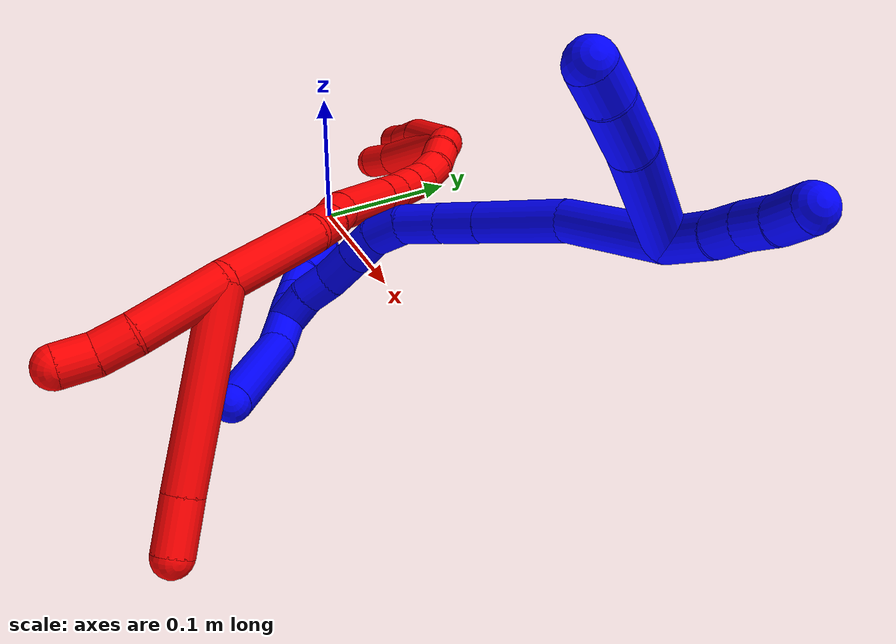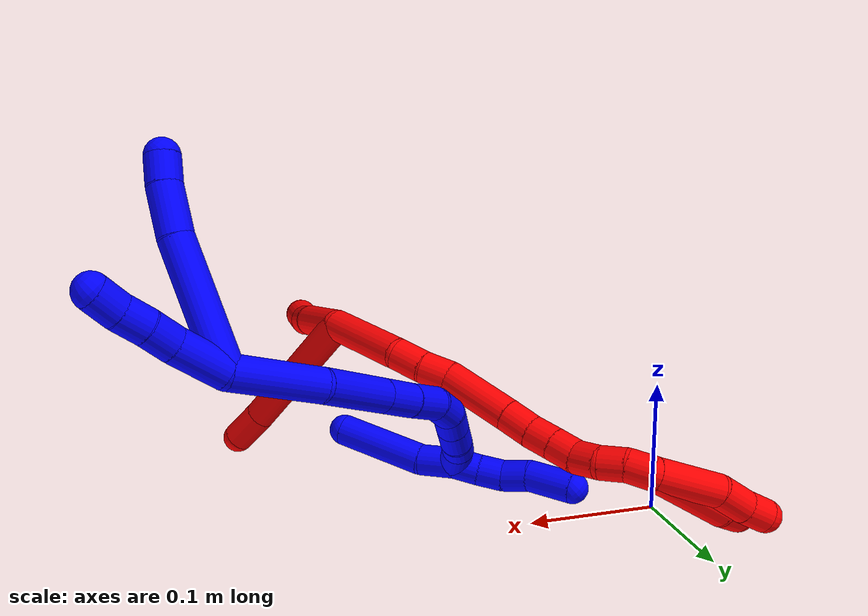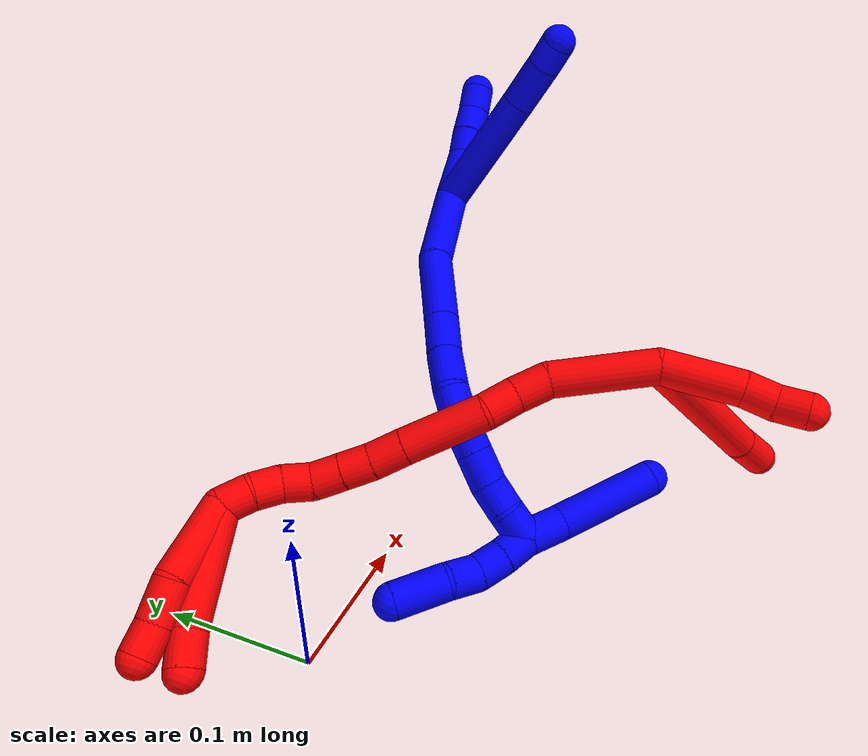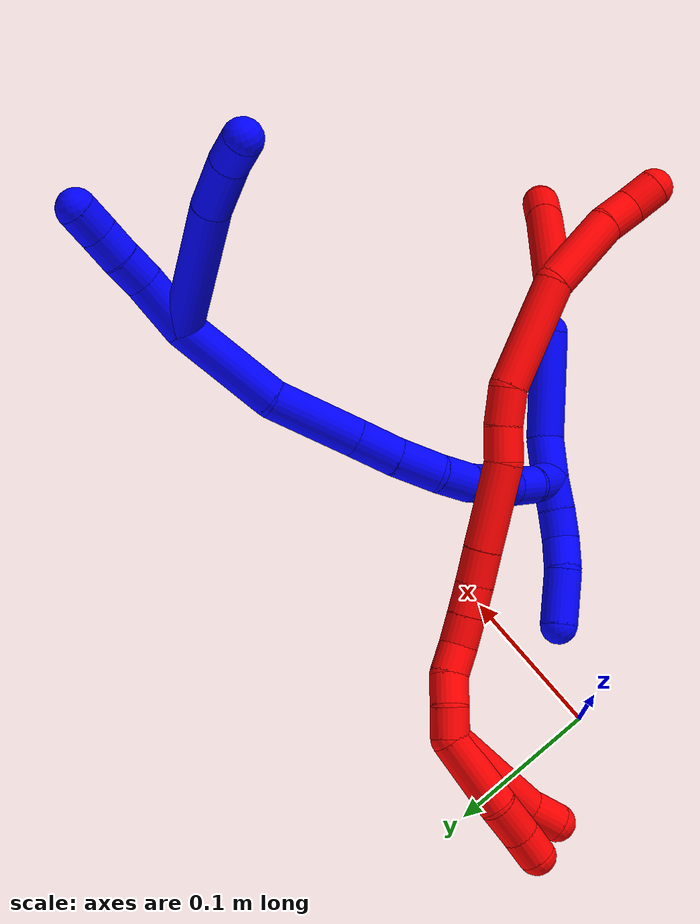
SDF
<sdf version="1.7">
 <world name="default">
  <plugin name="TubeGeneratorPlugin" filename="libtube_generator_plugin.so"/>
  <model name="photoneo_s_sensor">
   <static>1</static>
   <pose>0 0 2 1.57079 1.57079 3.14159</pose>
   <link name="link">
    <inertial><mass>0.1</mass></inertial>
    <sensor name="sensor" type="depth">
     <update_rate>30</update_rate>
     <camera>
      <horizontal_fov>1.22</horizontal_fov>
      <image><width>1920</width><height>1200</height><format>B8G8R8</format></image>
      <clip><near>0.1</near><far>4</far></clip>
      <depth_camera><output>points</output></depth_camera>
     </camera>
     <plugin name="camera_plugin" filename="libgazebo_ros_depth_camera.so">
      <baseline>0.2</baseline>
      <alwaysOn>1</alwaysOn>
      <updateRate>0.0</updateRate>
      <cameraName>camera_ir</cameraName>
      <imageTopicName>/camera/color/image_raw</imageTopicName>
      <cameraInfoTopicName>/camera/color/camera_info</cameraInfoTopicName>
      <depthImageTopicName>/camera/depth/image_raw</depthImageTopicName>
      <depthImageCameraInfoTopicName>/camera/depth/camera_info</depthImageCameraInfoTopicName>
      <pointCloudTopicName>/camera/depth/points</pointCloudTopicName>
      <frameName>fr_optical</frameName>
      <pointCloudCutoff>0.1</pointCloudCutoff>
      <pointCloudCutoffMax>2.0</pointCloudCutoffMax>
      <distortionK1>0</distortionK1>
      <distortionK2>0</distortionK2>
      <distortionK3>0</distortionK3>
      <distortionT1>0</distortionT1>
      <distortionT2>0</distortionT2>
      <CxPrime>0</CxPrime>
      <Cx>0</Cx>
      <Cy>0</Cy>
      <focalLength>0</focalLength>
      <hackBaseline>0</hackBaseline>
     </plugin>
    </sensor>
   </link>
  </model>
  <gravity>0 0 -9.8</gravity>
  <magnetic_field>6e-06 2.3e-05 -4.2e-05</magnetic_field>
  <atmosphere type="adiabatic"/>
  <physics name="default_physics" default="0" type="ode">
   <max_step_size>0.003</max_step_size>
   <real_time_factor>1</real_time_factor>
   <real_time_update_rate>1000</real_time_update_rate>
   <max_contacts>10000</max_contacts>
   <ode>
    <solver>
     <type>quick</type>
     <iters>100</iters>
     <sor>1.3</sor>
     <use_dynamic_moi_rescaling>0</use_dynamic_moi_rescaling>
    </solver>
    <constraints>
     <contact_max_correcting_vel>0</contact_max_correcting_vel>
     <contact_surface_layer>0.001</contact_surface_layer>
     <cfm>0</cfm>
     <erp>0.2</erp>
    </constraints>
   </ode>
  </physics>
  <scene><ambient>0.4 0.4 0.4 1</ambient><background>0.7 0.7 0.7 1</background><shadows>0</shadows></scene>
  <audio><device>default</device></audio>
  <spherical_coordinates>
   <surface_model>EARTH_WGS84</surface_model>
   <latitude_deg>0</latitude_deg>
   <longitude_deg>0</longitude_deg>
   <elevation>0</elevation>
   <heading_deg>0</heading_deg>
  </spherical_coordinates>
  <model name="bin">
   <static>1</static>
   <link name="bottom">
    <collision name="collision-bottom">
     <pose>0 0 -0.01 0 -0 0</pose>
     <geometry><box><size>0.8 0.6 0.02</size></box></geometry>
     <surface>
      <friction><ode><mu>100</mu><mu2>100</mu2></ode></friction>
      <contact><collide_bitmask>65535</collide_bitmask></contact>
     </surface>
    </collision>
   </link>
   <link name="west_wall">
    <collision name="collision-west_wall">
     <pose>-0.41 0 0.1 0 -0 0</pose>
     <geometry><box><size>0.02 0.6 0.2</size></box></geometry>
     <surface>
      <friction><ode><mu>100</mu><mu2>100</mu2></ode></friction>
      <contact><collide_bitmask>65535</collide_bitmask></contact>
     </surface>
    </collision>
   </link>
   <link name="east_wall">
    <collision name="collision-east_wall">
     <pose>0.41 0 0.1 0 -0 0</pose>
     <geometry><box><size>0.02 0.6 0.2</size></box></geometry>
     <surface>
      <friction><ode><mu>100</mu><mu2>100</mu2></ode></friction>
      <contact><collide_bitmask>65535</collide_bitmask></contact>
     </surface>
    </collision>
   </link>
   <link name="south_wall">
    <collision name="collision-south_wall">
     <pose>0 -0.31 0.1 0 -0 0</pose>
     <geometry><box><size>0.8 0.02 0.2</size></box></geometry>
     <surface>
      <friction><ode><mu>100</mu><mu2>100</mu2></ode></friction>
      <contact><collide_bitmask>65535</collide_bitmask></contact>
     </surface>
    </collision>
   </link>
   <link name="north_wall">
    <collision name="collision-north_wall">
     <pose>0 0.31 0.1 0 -0 0</pose>
     <geometry><box><size>0.8 0.02 0.2</size></box></geometry>
     <surface>
      <friction><ode><mu>100</mu><mu2>100</mu2></ode></friction>
      <contact><collide_bitmask>65535</collide_bitmask></contact>
     </surface>
    </collision>
   </link>
  </model>
  <model name="1">
   <static>0</static>
   <link name="1">
    <collision name="collision-cylinder-e_1_2_8">
     <pose>-0.022799 -0.006293 0.040173 0.155375 -0.511007 -0.040662</pose>
     <geometry><cylinder><radius>0.0125</radius><length>0.093235</length></cylinder></geometry>
     <surface>
      <friction><ode><mu>1.16</mu><mu2>1.16</mu2><slip1>0</slip1><slip2>0</slip2></ode></friction>
      <contact><ode><kp>1e+06</kp><kd>1</kd><max_vel>0</max_vel><min_depth>0.001</min_depth></ode></contact>
     </surface>
    </collision>
    <visual name="visual-cylinder-e_1_2_8">
     <pose>-0.022799 -0.006293 0.040173 0.155375 -0.511007 -0.040662</pose>
     <geometry><cylinder><radius>0.0125</radius><length>0.093235</length></cylinder></geometry>
     <material><ambient>0 0 1 1</ambient></material>
    </visual>
    <collision name="collision-cylinder-e_2_8_9">
     <pose>-0.056466 -0.014445 0.09463 0.129459 -0.646367 -0.043413</pose>
     <geometry><cylinder><radius>0.0125</radius><length>0.036091</length></cylinder></geometry>
     <surface>
      <friction><ode><mu>1.16</mu><mu2>1.16</mu2><slip1>0</slip1><slip2>0</slip2></ode></friction>
      <contact><ode><kp>1e+06</kp><kd>1</kd><max_vel>0</max_vel><min_depth>0.001</min_depth></ode></contact>
     </surface>
    </collision>
    <visual name="visual-cylinder-e_2_8_9">
     <pose>-0.056466 -0.014445 0.09463 0.129459 -0.646367 -0.043413</pose>
     <geometry><cylinder><radius>0.0125</radius><length>0.036091</length></cylinder></geometry>
     <material><ambient>0 0 1 1</ambient></material>
    </visual>
    <collision name="collision-cylinder-e_3_9_6">
     <pose>-0.074538 -0.016807 0.116311 0.067872 -0.771045 -0.027553</pose>
     <geometry><cylinder><radius>0.0125</radius><length>0.020673</length></cylinder></geometry>
     <surface>
      <friction><ode><mu>1.16</mu><mu2>1.16</mu2><slip1>0</slip1><slip2>0</slip2></ode></friction>
      <contact><ode><kp>1e+06</kp><kd>1</kd><max_vel>0</max_vel><min_depth>0.001</min_depth></ode></contact>
     </surface>
    </collision>
    <visual name="visual-cylinder-e_3_9_6">
     <pose>-0.074538 -0.016807 0.116311 0.067872 -0.771045 -0.027553</pose>
     <geometry><cylinder><radius>0.0125</radius><length>0.020673</length></cylinder></geometry>
     <material><ambient>0 0 1 1</ambient></material>
    </visual>
    <collision name="collision-cylinder-e_1_2_10">
     <pose>0.00683 0.00134 0.018038 -0.07416 0.361047 -0.013541</pose>
     <geometry><cylinder><radius>0.0125</radius><length>0.038668</length></cylinder></geometry>
     <surface>
      <friction><ode><mu>1.16</mu><mu2>1.16</mu2><slip1>0</slip1><slip2>0</slip2></ode></friction>
      <contact><ode><kp>1e+06</kp><kd>1</kd><max_vel>0</max_vel><min_depth>0.001</min_depth></ode></contact>
     </surface>
    </collision>
    <visual name="visual-cylinder-e_1_2_10">
     <pose>0.00683 0.00134 0.018038 -0.07416 0.361047 -0.013541</pose>
     <geometry><cylinder><radius>0.0125</radius><length>0.038668</length></cylinder></geometry>
     <material><ambient>0 0 1 1</ambient></material>
    </visual>
    <collision name="collision-cylinder-e_2_10_11">
     <pose>0.016817 0.00472 0.045662 -0.209658 0.311684 -0.033059</pose>
     <geometry><cylinder><radius>0.0125</radius><length>0.020596</length></cylinder></geometry>
     <surface>
      <friction><ode><mu>1.16</mu><mu2>1.16</mu2><slip1>0</slip1><slip2>0</slip2></ode></friction>
      <contact><ode><kp>1e+06</kp><kd>1</kd><max_vel>0</max_vel><min_depth>0.001</min_depth></ode></contact>
     </surface>
    </collision>
    <visual name="visual-cylinder-e_2_10_11">
     <pose>0.016817 0.00472 0.045662 -0.209658 0.311684 -0.033059</pose>
     <geometry><cylinder><radius>0.0125</radius><length>0.020596</length></cylinder></geometry>
     <material><ambient>0 0 1 1</ambient></material>
    </visual>
    <collision name="collision-cylinder-e_3_11_12">
     <pose>0.02348 0.007844 0.064694 -0.114275 0.353184 -0.020414</pose>
     <geometry><cylinder><radius>0.0125</radius><length>0.020264</length></cylinder></geometry>
     <surface>
      <friction><ode><mu>1.16</mu><mu2>1.16</mu2><slip1>0</slip1><slip2>0</slip2></ode></friction>
      <contact><ode><kp>1e+06</kp><kd>1</kd><max_vel>0</max_vel><min_depth>0.001</min_depth></ode></contact>
     </surface>
    </collision>
    <visual name="visual-cylinder-e_3_11_12">
     <pose>0.02348 0.007844 0.064694 -0.114275 0.353184 -0.020414</pose>
     <geometry><cylinder><radius>0.0125</radius><length>0.020264</length></cylinder></geometry>
     <material><ambient>0 0 1 1</ambient></material>
    </visual>
    <collision name="collision-cylinder-e_4_12_5">
     <pose>0.02945 0.011008 0.083854 -0.210866 0.243239 -0.025867</pose>
     <geometry><cylinder><radius>0.0125</radius><length>0.020472</length></cylinder></geometry>
     <surface>
      <friction><ode><mu>1.16</mu><mu2>1.16</mu2><slip1>0</slip1><slip2>0</slip2></ode></friction>
      <contact><ode><kp>1e+06</kp><kd>1</kd><max_vel>0</max_vel><min_depth>0.001</min_depth></ode></contact>
     </surface>
    </collision>
    <visual name="visual-cylinder-e_4_12_5">
     <pose>0.02945 0.011008 0.083854 -0.210866 0.243239 -0.025867</pose>
     <geometry><cylinder><radius>0.0125</radius><length>0.020472</length></cylinder></geometry>
     <material><ambient>0 0 1 1</ambient></material>
    </visual>
    <collision name="collision-cylinder-e_1_2_13">
     <pose>-0.022231 -0.001847 -0.026769 3.07271 -0.691893 -2.95099</pose>
     <geometry><cylinder><radius>0.0125</radius><length>0.069691</length></cylinder></geometry>
     <surface>
      <friction><ode><mu>1.16</mu><mu2>1.16</mu2><slip1>0</slip1><slip2>0</slip2></ode></friction>
      <contact><ode><kp>1e+06</kp><kd>1</kd><max_vel>0</max_vel><min_depth>0.001</min_depth></ode></contact>
     </surface>
    </collision>
    <visual name="visual-cylinder-e_1_2_13">
     <pose>-0.022231 -0.001847 -0.026769 3.07271 -0.691893 -2.95099</pose>
     <geometry><cylinder><radius>0.0125</radius><length>0.069691</length></cylinder></geometry>
     <material><ambient>0 0 1 1</ambient></material>
    </visual>
    <collision name="collision-cylinder-e_2_13_14">
     <pose>-0.063036 -0.012749 -0.073897 2.72311 -0.694881 -2.0809</pose>
     <geometry><cylinder><radius>0.0125</radius><length>0.058017</length></cylinder></geometry>
     <surface>
      <friction><ode><mu>1.16</mu><mu2>1.16</mu2><slip1>0</slip1><slip2>0</slip2></ode></friction>
      <contact><ode><kp>1e+06</kp><kd>1</kd><max_vel>0</max_vel><min_depth>0.001</min_depth></ode></contact>
     </surface>
    </collision>
    <visual name="visual-cylinder-e_2_13_14">
     <pose>-0.063036 -0.012749 -0.073897 2.72311 -0.694881 -2.0809</pose>
     <geometry><cylinder><radius>0.0125</radius><length>0.058017</length></cylinder></geometry>
     <material><ambient>0 0 1 1</ambient></material>
    </visual>
    <collision name="collision-cylinder-e_3_14_15">
     <pose>-0.090968 -0.026271 -0.104599 2.73388 -0.693152 -2.10181</pose>
     <geometry><cylinder><radius>0.0125</radius><length>0.029291</length></cylinder></geometry>
     <surface>
      <friction><ode><mu>1.16</mu><mu2>1.16</mu2><slip1>0</slip1><slip2>0</slip2></ode></friction>
      <contact><ode><kp>1e+06</kp><kd>1</kd><max_vel>0</max_vel><min_depth>0.001</min_depth></ode></contact>
     </surface>
    </collision>
    <visual name="visual-cylinder-e_3_14_15">
     <pose>-0.090968 -0.026271 -0.104599 2.73388 -0.693152 -2.10181</pose>
     <geometry><cylinder><radius>0.0125</radius><length>0.029291</length></cylinder></geometry>
     <material><ambient>0 0 1 1</ambient></material>
    </visual>
    <collision name="collision-cylinder-e_4_15_16">
     <pose>-0.110085 -0.036009 -0.124688 2.64584 -0.722052 -1.96059</pose>
     <geometry><cylinder><radius>0.0125</radius><length>0.029532</length></cylinder></geometry>
     <surface>
      <friction><ode><mu>1.16</mu><mu2>1.16</mu2><slip1>0</slip1><slip2>0</slip2></ode></friction>
      <contact><ode><kp>1e+06</kp><kd>1</kd><max_vel>0</max_vel><min_depth>0.001</min_depth></ode></contact>
     </surface>
    </collision>
    <visual name="visual-cylinder-e_4_15_16">
     <pose>-0.110085 -0.036009 -0.124688 2.64584 -0.722052 -1.96059</pose>
     <geometry><cylinder><radius>0.0125</radius><length>0.029532</length></cylinder></geometry>
     <material><ambient>0 0 1 1</ambient></material>
    </visual>
    <collision name="collision-cylinder-e_5_16_17">
     <pose>-0.125051 -0.047953 -0.143136 2.48735 -0.443312 -1.17254</pose>
     <geometry><cylinder><radius>0.0125</radius><length>0.024277</length></cylinder></geometry>
     <surface>
      <friction><ode><mu>1.16</mu><mu2>1.16</mu2><slip1>0</slip1><slip2>0</slip2></ode></friction>
      <contact><ode><kp>1e+06</kp><kd>1</kd><max_vel>0</max_vel><min_depth>0.001</min_depth></ode></contact>
     </surface>
    </collision>
    <visual name="visual-cylinder-e_5_16_17">
     <pose>-0.125051 -0.047953 -0.143136 2.48735 -0.443312 -1.17254</pose>
     <geometry><cylinder><radius>0.0125</radius><length>0.024277</length></cylinder></geometry>
     <material><ambient>0 0 1 1</ambient></material>
    </visual>
    <collision name="collision-cylinder-e_6_17_18">
     <pose>-0.131819 -0.062434 -0.158925 2.30791 -0.146976 -0.329518</pose>
     <geometry><cylinder><radius>0.0125</radius><length>0.02132</length></cylinder></geometry>
     <surface>
      <friction><ode><mu>1.16</mu><mu2>1.16</mu2><slip1>0</slip1><slip2>0</slip2></ode></friction>
      <contact><ode><kp>1e+06</kp><kd>1</kd><max_vel>0</max_vel><min_depth>0.001</min_depth></ode></contact>
     </surface>
    </collision>
    <visual name="visual-cylinder-e_6_17_18">
     <pose>-0.131819 -0.062434 -0.158925 2.30791 -0.146976 -0.329518</pose>
     <geometry><cylinder><radius>0.0125</radius><length>0.02132</length></cylinder></geometry>
     <material><ambient>0 0 1 1</ambient></material>
    </visual>
    <collision name="collision-cylinder-e_7_18_19">
     <pose>-0.13521 -0.078903 -0.173936 2.31167 -0.154656 -0.348201</pose>
     <geometry><cylinder><radius>0.0125</radius><length>0.02376</length></cylinder></geometry>
     <surface>
      <friction><ode><mu>1.16</mu><mu2>1.16</mu2><slip1>0</slip1><slip2>0</slip2></ode></friction>
      <contact><ode><kp>1e+06</kp><kd>1</kd><max_vel>0</max_vel><min_depth>0.001</min_depth></ode></contact>
     </surface>
    </collision>
    <visual name="visual-cylinder-e_7_18_19">
     <pose>-0.13521 -0.078903 -0.173936 2.31167 -0.154656 -0.348201</pose>
     <geometry><cylinder><radius>0.0125</radius><length>0.02376</length></cylinder></geometry>
     <material><ambient>0 0 1 1</ambient></material>
    </visual>
    <collision name="collision-cylinder-e_8_19_20">
     <pose>-0.139922 -0.09586 -0.18736 2.15641 -0.281815 -0.516755</pose>
     <geometry><cylinder><radius>0.0125</radius><length>0.020727</length></cylinder></geometry>
     <surface>
      <friction><ode><mu>1.16</mu><mu2>1.16</mu2><slip1>0</slip1><slip2>0</slip2></ode></friction>
      <contact><ode><kp>1e+06</kp><kd>1</kd><max_vel>0</max_vel><min_depth>0.001</min_depth></ode></contact>
     </surface>
    </collision>
    <visual name="visual-cylinder-e_8_19_20">
     <pose>-0.139922 -0.09586 -0.18736 2.15641 -0.281815 -0.516755</pose>
     <geometry><cylinder><radius>0.0125</radius><length>0.020727</length></cylinder></geometry>
     <material><ambient>0 0 1 1</ambient></material>
    </visual>
    <collision name="collision-cylinder-e_9_20_1">
     <pose>-0.143006 -0.114179 -0.19888 2.11153 -0.017259 -0.030492</pose>
     <geometry><cylinder><radius>0.0125</radius><length>0.023386</length></cylinder></geometry>
     <surface>
      <friction><ode><mu>1.16</mu><mu2>1.16</mu2><slip1>0</slip1><slip2>0</slip2></ode></friction>
      <contact><ode><kp>1e+06</kp><kd>1</kd><max_vel>0</max_vel><min_depth>0.001</min_depth></ode></contact>
     </surface>
    </collision>
    <visual name="visual-cylinder-e_9_20_1">
     <pose>-0.143006 -0.114179 -0.19888 2.11153 -0.017259 -0.030492</pose>
     <geometry><cylinder><radius>0.0125</radius><length>0.023386</length></cylinder></geometry>
     <material><ambient>0 0 1 1</ambient></material>
    </visual>
    <collision name="collision-cylinder-e_1_1_21">
     <pose>-0.146181 -0.11843 -0.213124 -2.52974 -0.287657 0.859879</pose>
     <geometry><cylinder><radius>0.0125</radius><length>0.020957</length></cylinder></geometry>
     <surface>
      <friction><ode><mu>1.16</mu><mu2>1.16</mu2><slip1>0</slip1><slip2>0</slip2></ode></friction>
      <contact><ode><kp>1e+06</kp><kd>1</kd><max_vel>0</max_vel><min_depth>0.001</min_depth></ode></contact>
     </surface>
    </collision>
    <visual name="visual-cylinder-e_1_1_21">
     <pose>-0.146181 -0.11843 -0.213124 -2.52974 -0.287657 0.859879</pose>
     <geometry><cylinder><radius>0.0125</radius><length>0.020957</length></cylinder></geometry>
     <material><ambient>0 0 1 1</ambient></material>
    </visual>
    <collision name="collision-cylinder-e_2_21_22">
     <pose>-0.151908 -0.106209 -0.228696 -2.42116 -0.274642 0.70329</pose>
     <geometry><cylinder><radius>0.0125</radius><length>0.020315</length></cylinder></geometry>
     <surface>
      <friction><ode><mu>1.16</mu><mu2>1.16</mu2><slip1>0</slip1><slip2>0</slip2></ode></friction>
      <contact><ode><kp>1e+06</kp><kd>1</kd><max_vel>0</max_vel><min_depth>0.001</min_depth></ode></contact>
     </surface>
    </collision>
    <visual name="visual-cylinder-e_2_21_22">
     <pose>-0.151908 -0.106209 -0.228696 -2.42116 -0.274642 0.70329</pose>
     <geometry><cylinder><radius>0.0125</radius><length>0.020315</length></cylinder></geometry>
     <material><ambient>0 0 1 1</ambient></material>
    </visual>
    <collision name="collision-cylinder-e_3_22_23">
     <pose>-0.158261 -0.090895 -0.241278 -2.10414 -0.33629 0.578048</pose>
     <geometry><cylinder><radius>0.0125</radius><length>0.021809</length></cylinder></geometry>
     <surface>
      <friction><ode><mu>1.16</mu><mu2>1.16</mu2><slip1>0</slip1><slip2>0</slip2></ode></friction>
      <contact><ode><kp>1e+06</kp><kd>1</kd><max_vel>0</max_vel><min_depth>0.001</min_depth></ode></contact>
     </surface>
    </collision>
    <visual name="visual-cylinder-e_3_22_23">
     <pose>-0.158261 -0.090895 -0.241278 -2.10414 -0.33629 0.578048</pose>
     <geometry><cylinder><radius>0.0125</radius><length>0.021809</length></cylinder></geometry>
     <material><ambient>0 0 1 1</ambient></material>
    </visual>
    <collision name="collision-cylinder-e_4_23_4">
     <pose>-0.163929 -0.067805 -0.25809 -2.25398 -0.112351 0.235464</pose>
     <geometry><cylinder><radius>0.0125</radius><length>0.036918</length></cylinder></geometry>
     <surface>
      <friction><ode><mu>1.16</mu><mu2>1.16</mu2><slip1>0</slip1><slip2>0</slip2></ode></friction>
      <contact><ode><kp>1e+06</kp><kd>1</kd><max_vel>0</max_vel><min_depth>0.001</min_depth></ode></contact>
     </surface>
    </collision>
    <visual name="visual-cylinder-e_4_23_4">
     <pose>-0.163929 -0.067805 -0.25809 -2.25398 -0.112351 0.235464</pose>
     <geometry><cylinder><radius>0.0125</radius><length>0.036918</length></cylinder></geometry>
     <material><ambient>0 0 1 1</ambient></material>
    </visual>
    <collision name="collision-cylinder-e_1_1_24">
     <pose>-0.138687 -0.134518 -0.196338 0.878113 0.325245 0.153801</pose>
     <geometry><cylinder><radius>0.0125</radius><length>0.028294</length></cylinder></geometry>
     <surface>
      <friction><ode><mu>1.16</mu><mu2>1.16</mu2><slip1>0</slip1><slip2>0</slip2></ode></friction>
      <contact><ode><kp>1e+06</kp><kd>1</kd><max_vel>0</max_vel><min_depth>0.001</min_depth></ode></contact>
     </surface>
    </collision>
    <visual name="visual-cylinder-e_1_1_24">
     <pose>-0.138687 -0.134518 -0.196338 0.878113 0.325245 0.153801</pose>
     <geometry><cylinder><radius>0.0125</radius><length>0.028294</length></cylinder></geometry>
     <material><ambient>0 0 1 1</ambient></material>
    </visual>
    <collision name="collision-cylinder-e_2_24_3">
     <pose>-0.130815 -0.169408 -0.161887 0.759342 0.093615 0.037378</pose>
     <geometry><cylinder><radius>0.0125</radius><length>0.071706</length></cylinder></geometry>
     <surface>
      <friction><ode><mu>1.16</mu><mu2>1.16</mu2><slip1>0</slip1><slip2>0</slip2></ode></friction>
      <contact><ode><kp>1e+06</kp><kd>1</kd><max_vel>0</max_vel><min_depth>0.001</min_depth></ode></contact>
     </surface>
    </collision>
    <visual name="visual-cylinder-e_2_24_3">
     <pose>-0.130815 -0.169408 -0.161887 0.759342 0.093615 0.037378</pose>
     <geometry><cylinder><radius>0.0125</radius><length>0.071706</length></cylinder></geometry>
     <material><ambient>0 0 1 1</ambient></material>
    </visual>
    <collision name="collision-sphere-3">
     <pose>-0.127464 -0.193983 -0.135997 0 -0 0</pose>
     <geometry><sphere><radius>0.0125</radius></sphere></geometry>
     <surface>
      <friction><ode><mu>1.16</mu><mu2>1.16</mu2><slip1>0</slip1><slip2>0</slip2></ode></friction>
      <contact><ode><kp>1e+06</kp><kd>1</kd><max_vel>0</max_vel><min_depth>0.001</min_depth></ode></contact>
     </surface>
    </collision>
    <visual name="visual-sphere-3">
     <pose>-0.127464 -0.193983 -0.135997 0 -0 0</pose>
     <geometry><sphere><radius>0.0125</radius></sphere></geometry>
     <material><ambient>0 0 1 1</ambient></material>
    </visual>
    <collision name="collision-sphere-24">
     <pose>-0.134167 -0.144834 -0.187777 0 -0 0</pose>
     <geometry><sphere><radius>0.0125</radius></sphere></geometry>
     <surface>
      <friction><ode><mu>1.16</mu><mu2>1.16</mu2><slip1>0</slip1><slip2>0</slip2></ode></friction>
      <contact><ode><kp>1e+06</kp><kd>1</kd><max_vel>0</max_vel><min_depth>0.001</min_depth></ode></contact>
     </surface>
    </collision>
    <visual name="visual-sphere-24">
     <pose>-0.134167 -0.144834 -0.187777 0 -0 0</pose>
     <geometry><sphere><radius>0.0125</radius></sphere></geometry>
     <material><ambient>0 0 1 1</ambient></material>
    </visual>
    <collision name="collision-sphere-4">
     <pose>-0.165999 -0.053579 -0.269669 0 -0 0</pose>
     <geometry><sphere><radius>0.0125</radius></sphere></geometry>
     <surface>
      <friction><ode><mu>1.16</mu><mu2>1.16</mu2><slip1>0</slip1><slip2>0</slip2></ode></friction>
      <contact><ode><kp>1e+06</kp><kd>1</kd><max_vel>0</max_vel><min_depth>0.001</min_depth></ode></contact>
     </surface>
    </collision>
    <visual name="visual-sphere-4">
     <pose>-0.165999 -0.053579 -0.269669 0 -0 0</pose>
     <geometry><sphere><radius>0.0125</radius></sphere></geometry>
     <material><ambient>0 0 1 1</ambient></material>
    </visual>
    <collision name="collision-sphere-23">
     <pose>-0.16186 -0.082031 -0.246511 0 -0 0</pose>
     <geometry><sphere><radius>0.0125</radius></sphere></geometry>
     <surface>
      <friction><ode><mu>1.16</mu><mu2>1.16</mu2><slip1>0</slip1><slip2>0</slip2></ode></friction>
      <contact><ode><kp>1e+06</kp><kd>1</kd><max_vel>0</max_vel><min_depth>0.001</min_depth></ode></contact>
     </surface>
    </collision>
    <visual name="visual-sphere-23">
     <pose>-0.16186 -0.082031 -0.246511 0 -0 0</pose>
     <geometry><sphere><radius>0.0125</radius></sphere></geometry>
     <material><ambient>0 0 1 1</ambient></material>
    </visual>
    <collision name="collision-sphere-22">
     <pose>-0.154663 -0.099759 -0.236044 0 -0 0</pose>
     <geometry><sphere><radius>0.0125</radius></sphere></geometry>
     <surface>
      <friction><ode><mu>1.16</mu><mu2>1.16</mu2><slip1>0</slip1><slip2>0</slip2></ode></friction>
      <contact><ode><kp>1e+06</kp><kd>1</kd><max_vel>0</max_vel><min_depth>0.001</min_depth></ode></contact>
     </surface>
    </collision>
    <visual name="visual-sphere-22">
     <pose>-0.154663 -0.099759 -0.236044 0 -0 0</pose>
     <geometry><sphere><radius>0.0125</radius></sphere></geometry>
     <material><ambient>0 0 1 1</ambient></material>
    </visual>
    <collision name="collision-sphere-21">
     <pose>-0.149153 -0.112659 -0.221349 0 -0 0</pose>
     <geometry><sphere><radius>0.0125</radius></sphere></geometry>
     <surface>
      <friction><ode><mu>1.16</mu><mu2>1.16</mu2><slip1>0</slip1><slip2>0</slip2></ode></friction>
      <contact><ode><kp>1e+06</kp><kd>1</kd><max_vel>0</max_vel><min_depth>0.001</min_depth></ode></contact>
     </surface>
    </collision>
    <visual name="visual-sphere-21">
     <pose>-0.149153 -0.112659 -0.221349 0 -0 0</pose>
     <geometry><sphere><radius>0.0125</radius></sphere></geometry>
     <material><ambient>0 0 1 1</ambient></material>
    </visual>
    <collision name="collision-sphere-1">
     <pose>-0.143208 -0.124202 -0.204898 0 -0 0</pose>
     <geometry><sphere><radius>0.0125</radius></sphere></geometry>
     <surface>
      <friction><ode><mu>1.16</mu><mu2>1.16</mu2><slip1>0</slip1><slip2>0</slip2></ode></friction>
      <contact><ode><kp>1e+06</kp><kd>1</kd><max_vel>0</max_vel><min_depth>0.001</min_depth></ode></contact>
     </surface>
    </collision>
    <visual name="visual-sphere-1">
     <pose>-0.143208 -0.124202 -0.204898 0 -0 0</pose>
     <geometry><sphere><radius>0.0125</radius></sphere></geometry>
     <material><ambient>0 0 1 1</ambient></material>
    </visual>
    <collision name="collision-sphere-11">
     <pose>0.019975 0.00676 0.055249 0 -0 0</pose>
     <geometry><sphere><radius>0.0125</radius></sphere></geometry>
     <surface>
      <friction><ode><mu>1.16</mu><mu2>1.16</mu2><slip1>0</slip1><slip2>0</slip2></ode></friction>
      <contact><ode><kp>1e+06</kp><kd>1</kd><max_vel>0</max_vel><min_depth>0.001</min_depth></ode></contact>
     </surface>
    </collision>
    <visual name="visual-sphere-11">
     <pose>0.019975 0.00676 0.055249 0 -0 0</pose>
     <geometry><sphere><radius>0.0125</radius></sphere></geometry>
     <material><ambient>0 0 1 1</ambient></material>
    </visual>
    <collision name="collision-sphere-10">
     <pose>0.013659 0.00268 0.036075 0 -0 0</pose>
     <geometry><sphere><radius>0.0125</radius></sphere></geometry>
     <surface>
      <friction><ode><mu>1.16</mu><mu2>1.16</mu2><slip1>0</slip1><slip2>0</slip2></ode></friction>
      <contact><ode><kp>1e+06</kp><kd>1</kd><max_vel>0</max_vel><min_depth>0.001</min_depth></ode></contact>
     </surface>
    </collision>
    <visual name="visual-sphere-10">
     <pose>0.013659 0.00268 0.036075 0 -0 0</pose>
     <geometry><sphere><radius>0.0125</radius></sphere></geometry>
     <material><ambient>0 0 1 1</ambient></material>
    </visual>
    <collision name="collision-sphere-6">
     <pose>-0.081742 -0.01731 0.123707 0 -0 0</pose>
     <geometry><sphere><radius>0.0125</radius></sphere></geometry>
     <surface>
      <friction><ode><mu>1.16</mu><mu2>1.16</mu2><slip1>0</slip1><slip2>0</slip2></ode></friction>
      <contact><ode><kp>1e+06</kp><kd>1</kd><max_vel>0</max_vel><min_depth>0.001</min_depth></ode></contact>
     </surface>
    </collision>
    <visual name="visual-sphere-6">
     <pose>-0.081742 -0.01731 0.123707 0 -0 0</pose>
     <geometry><sphere><radius>0.0125</radius></sphere></geometry>
     <material><ambient>0 0 1 1</ambient></material>
    </visual>
    <collision name="collision-sphere-9">
     <pose>-0.067335 -0.016305 0.108915 0 -0 0</pose>
     <geometry><sphere><radius>0.0125</radius></sphere></geometry>
     <surface>
      <friction><ode><mu>1.16</mu><mu2>1.16</mu2><slip1>0</slip1><slip2>0</slip2></ode></friction>
      <contact><ode><kp>1e+06</kp><kd>1</kd><max_vel>0</max_vel><min_depth>0.001</min_depth></ode></contact>
     </surface>
    </collision>
    <visual name="visual-sphere-9">
     <pose>-0.067335 -0.016305 0.108915 0 -0 0</pose>
     <geometry><sphere><radius>0.0125</radius></sphere></geometry>
     <material><ambient>0 0 1 1</ambient></material>
    </visual>
    <collision name="collision-sphere-2">
     <geometry><sphere><radius>0.0125</radius></sphere></geometry>
     <surface>
      <friction><ode><mu>1.16</mu><mu2>1.16</mu2><slip1>0</slip1><slip2>0</slip2></ode></friction>
      <contact><ode><kp>1e+06</kp><kd>1</kd><max_vel>0</max_vel><min_depth>0.001</min_depth></ode></contact>
     </surface>
    </collision>
    <visual name="visual-sphere-2">
     <geometry><sphere><radius>0.0125</radius></sphere></geometry>
     <material><ambient>0 0 1 1</ambient></material>
    </visual>
    <collision name="collision-sphere-19">
     <pose>-0.13704 -0.087564 -0.181858 0 -0 0</pose>
     <geometry><sphere><radius>0.0125</radius></sphere></geometry>
     <surface>
      <friction><ode><mu>1.16</mu><mu2>1.16</mu2><slip1>0</slip1><slip2>0</slip2></ode></friction>
      <contact><ode><kp>1e+06</kp><kd>1</kd><max_vel>0</max_vel><min_depth>0.001</min_depth></ode></contact>
     </surface>
    </collision>
    <visual name="visual-sphere-19">
     <pose>-0.13704 -0.087564 -0.181858 0 -0 0</pose>
     <geometry><sphere><radius>0.0125</radius></sphere></geometry>
     <material><ambient>0 0 1 1</ambient></material>
    </visual>
    <collision name="collision-sphere-8">
     <pose>-0.045597 -0.012585 0.080345 0 -0 0</pose>
     <geometry><sphere><radius>0.0125</radius></sphere></geometry>
     <surface>
      <friction><ode><mu>1.16</mu><mu2>1.16</mu2><slip1>0</slip1><slip2>0</slip2></ode></friction>
      <contact><ode><kp>1e+06</kp><kd>1</kd><max_vel>0</max_vel><min_depth>0.001</min_depth></ode></contact>
     </surface>
    </collision>
    <visual name="visual-sphere-8">
     <pose>-0.045597 -0.012585 0.080345 0 -0 0</pose>
     <geometry><sphere><radius>0.0125</radius></sphere></geometry>
     <material><ambient>0 0 1 1</ambient></material>
    </visual>
    <collision name="collision-sphere-12">
     <pose>0.026985 0.008928 0.074139 0 -0 0</pose>
     <geometry><sphere><radius>0.0125</radius></sphere></geometry>
     <surface>
      <friction><ode><mu>1.16</mu><mu2>1.16</mu2><slip1>0</slip1><slip2>0</slip2></ode></friction>
      <contact><ode><kp>1e+06</kp><kd>1</kd><max_vel>0</max_vel><min_depth>0.001</min_depth></ode></contact>
     </surface>
    </collision>
    <visual name="visual-sphere-12">
     <pose>0.026985 0.008928 0.074139 0 -0 0</pose>
     <geometry><sphere><radius>0.0125</radius></sphere></geometry>
     <material><ambient>0 0 1 1</ambient></material>
    </visual>
    <collision name="collision-sphere-5">
     <pose>0.031915 0.013087 0.093568 0 -0 0</pose>
     <geometry><sphere><radius>0.0125</radius></sphere></geometry>
     <surface>
      <friction><ode><mu>1.16</mu><mu2>1.16</mu2><slip1>0</slip1><slip2>0</slip2></ode></friction>
      <contact><ode><kp>1e+06</kp><kd>1</kd><max_vel>0</max_vel><min_depth>0.001</min_depth></ode></contact>
     </surface>
    </collision>
    <visual name="visual-sphere-5">
     <pose>0.031915 0.013087 0.093568 0 -0 0</pose>
     <geometry><sphere><radius>0.0125</radius></sphere></geometry>
     <material><ambient>0 0 1 1</ambient></material>
    </visual>
    <collision name="collision-sphere-13">
     <pose>-0.044462 -0.003694 -0.053537 0 -0 0</pose>
     <geometry><sphere><radius>0.0125</radius></sphere></geometry>
     <surface>
      <friction><ode><mu>1.16</mu><mu2>1.16</mu2><slip1>0</slip1><slip2>0</slip2></ode></friction>
      <contact><ode><kp>1e+06</kp><kd>1</kd><max_vel>0</max_vel><min_depth>0.001</min_depth></ode></contact>
     </surface>
    </collision>
    <visual name="visual-sphere-13">
     <pose>-0.044462 -0.003694 -0.053537 0 -0 0</pose>
     <geometry><sphere><radius>0.0125</radius></sphere></geometry>
     <material><ambient>0 0 1 1</ambient></material>
    </visual>
    <collision name="collision-sphere-14">
     <pose>-0.08161 -0.021804 -0.094257 0 -0 0</pose>
     <geometry><sphere><radius>0.0125</radius></sphere></geometry>
     <surface>
      <friction><ode><mu>1.16</mu><mu2>1.16</mu2><slip1>0</slip1><slip2>0</slip2></ode></friction>
      <contact><ode><kp>1e+06</kp><kd>1</kd><max_vel>0</max_vel><min_depth>0.001</min_depth></ode></contact>
     </surface>
    </collision>
    <visual name="visual-sphere-14">
     <pose>-0.08161 -0.021804 -0.094257 0 -0 0</pose>
     <geometry><sphere><radius>0.0125</radius></sphere></geometry>
     <material><ambient>0 0 1 1</ambient></material>
    </visual>
    <collision name="collision-sphere-15">
     <pose>-0.100326 -0.030738 -0.114941 0 -0 0</pose>
     <geometry><sphere><radius>0.0125</radius></sphere></geometry>
     <surface>
      <friction><ode><mu>1.16</mu><mu2>1.16</mu2><slip1>0</slip1><slip2>0</slip2></ode></friction>
      <contact><ode><kp>1e+06</kp><kd>1</kd><max_vel>0</max_vel><min_depth>0.001</min_depth></ode></contact>
     </surface>
    </collision>
    <visual name="visual-sphere-15">
     <pose>-0.100326 -0.030738 -0.114941 0 -0 0</pose>
     <geometry><sphere><radius>0.0125</radius></sphere></geometry>
     <material><ambient>0 0 1 1</ambient></material>
    </visual>
    <collision name="collision-sphere-16">
     <pose>-0.119845 -0.04128 -0.134435 0 -0 0</pose>
     <geometry><sphere><radius>0.0125</radius></sphere></geometry>
     <surface>
      <friction><ode><mu>1.16</mu><mu2>1.16</mu2><slip1>0</slip1><slip2>0</slip2></ode></friction>
      <contact><ode><kp>1e+06</kp><kd>1</kd><max_vel>0</max_vel><min_depth>0.001</min_depth></ode></contact>
     </surface>
    </collision>
    <visual name="visual-sphere-16">
     <pose>-0.119845 -0.04128 -0.134435 0 -0 0</pose>
     <geometry><sphere><radius>0.0125</radius></sphere></geometry>
     <material><ambient>0 0 1 1</ambient></material>
    </visual>
    <collision name="collision-sphere-17">
     <pose>-0.130258 -0.054626 -0.151837 0 -0 0</pose>
     <geometry><sphere><radius>0.0125</radius></sphere></geometry>
     <surface>
      <friction><ode><mu>1.16</mu><mu2>1.16</mu2><slip1>0</slip1><slip2>0</slip2></ode></friction>
      <contact><ode><kp>1e+06</kp><kd>1</kd><max_vel>0</max_vel><min_depth>0.001</min_depth></ode></contact>
     </surface>
    </collision>
    <visual name="visual-sphere-17">
     <pose>-0.130258 -0.054626 -0.151837 0 -0 0</pose>
     <geometry><sphere><radius>0.0125</radius></sphere></geometry>
     <material><ambient>0 0 1 1</ambient></material>
    </visual>
    <collision name="collision-sphere-18">
     <pose>-0.13338 -0.070241 -0.166013 0 -0 0</pose>
     <geometry><sphere><radius>0.0125</radius></sphere></geometry>
     <surface>
      <friction><ode><mu>1.16</mu><mu2>1.16</mu2><slip1>0</slip1><slip2>0</slip2></ode></friction>
      <contact><ode><kp>1e+06</kp><kd>1</kd><max_vel>0</max_vel><min_depth>0.001</min_depth></ode></contact>
     </surface>
    </collision>
    <visual name="visual-sphere-18">
     <pose>-0.13338 -0.070241 -0.166013 0 -0 0</pose>
     <geometry><sphere><radius>0.0125</radius></sphere></geometry>
     <material><ambient>0 0 1 1</ambient></material>
    </visual>
    <collision name="collision-sphere-20">
     <pose>-0.142804 -0.104156 -0.192862 0 -0 0</pose>
     <geometry><sphere><radius>0.0125</radius></sphere></geometry>
     <surface>
      <friction><ode><mu>1.16</mu><mu2>1.16</mu2><slip1>0</slip1><slip2>0</slip2></ode></friction>
      <contact><ode><kp>1e+06</kp><kd>1</kd><max_vel>0</max_vel><min_depth>0.001</min_depth></ode></contact>
     </surface>
    </collision>
    <visual name="visual-sphere-20">
     <pose>-0.142804 -0.104156 -0.192862 0 -0 0</pose>
     <geometry><sphere><radius>0.0125</radius></sphere></geometry>
     <material><ambient>0 0 1 1</ambient></material>
    </visual>
    <inertial>
     <pose>-0.079197 -0.050306 -0.079019 0 -0 0</pose>
     <mass>0.75</mass>
     <inertia><ixx>6e-05</ixx><ixy>0</ixy><ixz>0</ixz><iyy>0.000121</iyy><iyz>0</iyz><izz>0.000116</izz></inertia>
    </inertial>
   </link>
   <pose>0.327385 0.052424 0.159691 0.520986 0.503008 0.603069</pose>
  </model>
  <model name="2">
   <static>0</static>
   <link name="2">
    <collision name="collision-cylinder-e_1_2_8">
     <pose>0.057897 0.006328 0.006534 -0.769386 1.41496 -0.666613</pose>
     <geometry><cylinder><radius>0.0125</radius><length>0.117214</length></cylinder></geometry>
     <surface>
      <friction><ode><mu>1.16</mu><mu2>1.16</mu2><slip1>0</slip1><slip2>0</slip2></ode></friction>
      <contact><ode><kp>1e+06</kp><kd>1</kd><max_vel>0</max_vel><min_depth>0.001</min_depth></ode></contact>
     </surface>
    </collision>
    <visual name="visual-cylinder-e_1_2_8">
     <pose>0.057897 0.006328 0.006534 -0.769386 1.41496 -0.666613</pose>
     <geometry><cylinder><radius>0.0125</radius><length>0.117214</length></cylinder></geometry>
     <material><ambient>1 0 0 1</ambient></material>
    </visual>
    <collision name="collision-cylinder-e_2_8_6">
     <pose>0.131849 0.014365 0.015905 -0.542091 1.36734 -0.445306</pose>
     <geometry><cylinder><radius>0.0125</radius><length>0.032786</length></cylinder></geometry>
     <surface>
      <friction><ode><mu>1.16</mu><mu2>1.16</mu2><slip1>0</slip1><slip2>0</slip2></ode></friction>
      <contact><ode><kp>1e+06</kp><kd>1</kd><max_vel>0</max_vel><min_depth>0.001</min_depth></ode></contact>
     </surface>
    </collision>
    <visual name="visual-cylinder-e_2_8_6">
     <pose>0.131849 0.014365 0.015905 -0.542091 1.36734 -0.445306</pose>
     <geometry><cylinder><radius>0.0125</radius><length>0.032786</length></cylinder></geometry>
     <material><ambient>1 0 0 1</ambient></material>
    </visual>
    <collision name="collision-cylinder-e_1_2_9">
     <pose>0.020378 -0.019028 0.000604 1.53906 0.819394 0.796448</pose>
     <geometry><cylinder><radius>0.0125</radius><length>0.055773</length></cylinder></geometry>
     <surface>
      <friction><ode><mu>1.16</mu><mu2>1.16</mu2><slip1>0</slip1><slip2>0</slip2></ode></friction>
      <contact><ode><kp>1e+06</kp><kd>1</kd><max_vel>0</max_vel><min_depth>0.001</min_depth></ode></contact>
     </surface>
    </collision>
    <visual name="visual-cylinder-e_1_2_9">
     <pose>0.020378 -0.019028 0.000604 1.53906 0.819394 0.796448</pose>
     <geometry><cylinder><radius>0.0125</radius><length>0.055773</length></cylinder></geometry>
     <material><ambient>1 0 0 1</ambient></material>
    </visual>
    <collision name="collision-cylinder-e_2_9_10">
     <pose>0.048937 -0.045603 -0.000641 1.81115 0.811164 1.00159</pose>
     <geometry><cylinder><radius>0.0125</radius><length>0.022568</length></cylinder></geometry>
     <surface>
      <friction><ode><mu>1.16</mu><mu2>1.16</mu2><slip1>0</slip1><slip2>0</slip2></ode></friction>
      <contact><ode><kp>1e+06</kp><kd>1</kd><max_vel>0</max_vel><min_depth>0.001</min_depth></ode></contact>
     </surface>
    </collision>
    <visual name="visual-cylinder-e_2_9_10">
     <pose>0.048937 -0.045603 -0.000641 1.81115 0.811164 1.00159</pose>
     <geometry><cylinder><radius>0.0125</radius><length>0.022568</length></cylinder></geometry>
     <material><ambient>1 0 0 1</ambient></material>
    </visual>
    <collision name="collision-cylinder-e_3_10_5">
     <pose>0.063185 -0.062053 -0.003595 1.69412 0.594568 0.667429</pose>
     <geometry><cylinder><radius>0.0125</radius><length>0.021659</length></cylinder></geometry>
     <surface>
      <friction><ode><mu>1.16</mu><mu2>1.16</mu2><slip1>0</slip1><slip2>0</slip2></ode></friction>
      <contact><ode><kp>1e+06</kp><kd>1</kd><max_vel>0</max_vel><min_depth>0.001</min_depth></ode></contact>
     </surface>
    </collision>
    <visual name="visual-cylinder-e_3_10_5">
     <pose>0.063185 -0.062053 -0.003595 1.69412 0.594568 0.667429</pose>
     <geometry><cylinder><radius>0.0125</radius><length>0.021659</length></cylinder></geometry>
     <material><ambient>1 0 0 1</ambient></material>
    </visual>
    <collision name="collision-cylinder-e_1_2_11">
     <pose>-0.021047 0.026731 -0.013457 -2.03718 -0.612914 0.948869</pose>
     <geometry><cylinder><radius>0.0125</radius><length>0.073174</length></cylinder></geometry>
     <surface>
      <friction><ode><mu>1.16</mu><mu2>1.16</mu2><slip1>0</slip1><slip2>0</slip2></ode></friction>
      <contact><ode><kp>1e+06</kp><kd>1</kd><max_vel>0</max_vel><min_depth>0.001</min_depth></ode></contact>
     </surface>
    </collision>
    <visual name="visual-cylinder-e_1_2_11">
     <pose>-0.021047 0.026731 -0.013457 -2.03718 -0.612914 0.948869</pose>
     <geometry><cylinder><radius>0.0125</radius><length>0.073174</length></cylinder></geometry>
     <material><ambient>1 0 0 1</ambient></material>
    </visual>
    <collision name="collision-cylinder-e_2_11_12">
     <pose>-0.04723 0.061297 -0.034758 -2.3568 -0.433853 0.97867</pose>
     <geometry><cylinder><radius>0.0125</radius><length>0.024438</length></cylinder></geometry>
     <surface>
      <friction><ode><mu>1.16</mu><mu2>1.16</mu2><slip1>0</slip1><slip2>0</slip2></ode></friction>
      <contact><ode><kp>1e+06</kp><kd>1</kd><max_vel>0</max_vel><min_depth>0.001</min_depth></ode></contact>
     </surface>
    </collision>
    <visual name="visual-cylinder-e_2_11_12">
     <pose>-0.04723 0.061297 -0.034758 -2.3568 -0.433853 0.97867</pose>
     <geometry><cylinder><radius>0.0125</radius><length>0.024438</length></cylinder></geometry>
     <material><ambient>1 0 0 1</ambient></material>
    </visual>
    <collision name="collision-cylinder-e_3_12_13">
     <pose>-0.057308 0.075095 -0.050971 -2.52242 -0.448236 1.23829</pose>
     <geometry><cylinder><radius>0.0125</radius><length>0.022803</length></cylinder></geometry>
     <surface>
      <friction><ode><mu>1.16</mu><mu2>1.16</mu2><slip1>0</slip1><slip2>0</slip2></ode></friction>
      <contact><ode><kp>1e+06</kp><kd>1</kd><max_vel>0</max_vel><min_depth>0.001</min_depth></ode></contact>
     </surface>
    </collision>
    <visual name="visual-cylinder-e_3_12_13">
     <pose>-0.057308 0.075095 -0.050971 -2.52242 -0.448236 1.23829</pose>
     <geometry><cylinder><radius>0.0125</radius><length>0.022803</length></cylinder></geometry>
     <material><ambient>1 0 0 1</ambient></material>
    </visual>
    <collision name="collision-cylinder-e_4_13_14">
     <pose>-0.072809 0.101643 -0.075407 -2.2336 -0.384279 0.758688</pose>
     <geometry><cylinder><radius>0.0125</radius><length>0.056336</length></cylinder></geometry>
     <surface>
      <friction><ode><mu>1.16</mu><mu2>1.16</mu2><slip1>0</slip1><slip2>0</slip2></ode></friction>
      <contact><ode><kp>1e+06</kp><kd>1</kd><max_vel>0</max_vel><min_depth>0.001</min_depth></ode></contact>
     </surface>
    </collision>
    <visual name="visual-cylinder-e_4_13_14">
     <pose>-0.072809 0.101643 -0.075407 -2.2336 -0.384279 0.758688</pose>
     <geometry><cylinder><radius>0.0125</radius><length>0.056336</length></cylinder></geometry>
     <material><ambient>1 0 0 1</ambient></material>
    </visual>
    <collision name="collision-cylinder-e_5_14_15">
     <pose>-0.087399 0.130631 -0.098149 -2.24195 -0.359301 0.719519</pose>
     <geometry><cylinder><radius>0.0125</radius><length>0.022925</length></cylinder></geometry>
     <surface>
      <friction><ode><mu>1.16</mu><mu2>1.16</mu2><slip1>0</slip1><slip2>0</slip2></ode></friction>
      <contact><ode><kp>1e+06</kp><kd>1</kd><max_vel>0</max_vel><min_depth>0.001</min_depth></ode></contact>
     </surface>
    </collision>
    <visual name="visual-cylinder-e_5_14_15">
     <pose>-0.087399 0.130631 -0.098149 -2.24195 -0.359301 0.719519</pose>
     <geometry><cylinder><radius>0.0125</radius><length>0.022925</length></cylinder></geometry>
     <material><ambient>1 0 0 1</ambient></material>
    </visual>
    <collision name="collision-cylinder-e_6_15_16">
     <pose>-0.096036 0.146206 -0.110269 -2.22028 -0.472825 0.9039</pose>
     <geometry><cylinder><radius>0.0125</radius><length>0.020232</length></cylinder></geometry>
     <surface>
      <friction><ode><mu>1.16</mu><mu2>1.16</mu2><slip1>0</slip1><slip2>0</slip2></ode></friction>
      <contact><ode><kp>1e+06</kp><kd>1</kd><max_vel>0</max_vel><min_depth>0.001</min_depth></ode></contact>
     </surface>
    </collision>
    <visual name="visual-cylinder-e_6_15_16">
     <pose>-0.096036 0.146206 -0.110269 -2.22028 -0.472825 0.9039</pose>
     <geometry><cylinder><radius>0.0125</radius><length>0.020232</length></cylinder></geometry>
     <material><ambient>1 0 0 1</ambient></material>
    </visual>
    <collision name="collision-cylinder-e_7_16_17">
     <pose>-0.105117 0.160592 -0.121009 -2.20388 -0.463602 0.872161</pose>
     <geometry><cylinder><radius>0.0125</radius><length>0.020007</length></cylinder></geometry>
     <surface>
      <friction><ode><mu>1.16</mu><mu2>1.16</mu2><slip1>0</slip1><slip2>0</slip2></ode></friction>
      <contact><ode><kp>1e+06</kp><kd>1</kd><max_vel>0</max_vel><min_depth>0.001</min_depth></ode></contact>
     </surface>
    </collision>
    <visual name="visual-cylinder-e_7_16_17">
     <pose>-0.105117 0.160592 -0.121009 -2.20388 -0.463602 0.872161</pose>
     <geometry><cylinder><radius>0.0125</radius><length>0.020007</length></cylinder></geometry>
     <material><ambient>1 0 0 1</ambient></material>
    </visual>
    <collision name="collision-cylinder-e_8_17_18">
     <pose>-0.116604 0.17379 -0.130264 -2.15559 -0.773984 1.29793</pose>
     <geometry><cylinder><radius>0.0125</radius><length>0.020069</length></cylinder></geometry>
     <surface>
      <friction><ode><mu>1.16</mu><mu2>1.16</mu2><slip1>0</slip1><slip2>0</slip2></ode></friction>
      <contact><ode><kp>1e+06</kp><kd>1</kd><max_vel>0</max_vel><min_depth>0.001</min_depth></ode></contact>
     </surface>
    </collision>
    <visual name="visual-cylinder-e_8_17_18">
     <pose>-0.116604 0.17379 -0.130264 -2.15559 -0.773984 1.29793</pose>
     <geometry><cylinder><radius>0.0125</radius><length>0.020069</length></cylinder></geometry>
     <material><ambient>1 0 0 1</ambient></material>
    </visual>
    <collision name="collision-cylinder-e_9_18_19">
     <pose>-0.130391 0.183545 -0.140549 -2.60369 -0.743704 1.91111</pose>
     <geometry><cylinder><radius>0.0125</radius><length>0.020009</length></cylinder></geometry>
     <surface>
      <friction><ode><mu>1.16</mu><mu2>1.16</mu2><slip1>0</slip1><slip2>0</slip2></ode></friction>
      <contact><ode><kp>1e+06</kp><kd>1</kd><max_vel>0</max_vel><min_depth>0.001</min_depth></ode></contact>
     </surface>
    </collision>
    <visual name="visual-cylinder-e_9_18_19">
     <pose>-0.130391 0.183545 -0.140549 -2.60369 -0.743704 1.91111</pose>
     <geometry><cylinder><radius>0.0125</radius><length>0.020009</length></cylinder></geometry>
     <material><ambient>1 0 0 1</ambient></material>
    </visual>
    <collision name="collision-cylinder-e_10_19_1">
     <pose>-0.14211 0.192311 -0.153991 -2.52986 -0.517113 1.39444</pose>
     <geometry><cylinder><radius>0.0125</radius><length>0.020007</length></cylinder></geometry>
     <surface>
      <friction><ode><mu>1.16</mu><mu2>1.16</mu2><slip1>0</slip1><slip2>0</slip2></ode></friction>
      <contact><ode><kp>1e+06</kp><kd>1</kd><max_vel>0</max_vel><min_depth>0.001</min_depth></ode></contact>
     </surface>
    </collision>
    <visual name="visual-cylinder-e_10_19_1">
     <pose>-0.14211 0.192311 -0.153991 -2.52986 -0.517113 1.39444</pose>
     <geometry><cylinder><radius>0.0125</radius><length>0.020007</length></cylinder></geometry>
     <material><ambient>1 0 0 1</ambient></material>
    </visual>
    <collision name="collision-cylinder-e_1_1_20">
     <pose>-0.150123 0.19935 -0.187297 -3.06367 -0.11626 1.96127</pose>
     <geometry><cylinder><radius>0.0125</radius><length>0.052893</length></cylinder></geometry>
     <surface>
      <friction><ode><mu>1.16</mu><mu2>1.16</mu2><slip1>0</slip1><slip2>0</slip2></ode></friction>
      <contact><ode><kp>1e+06</kp><kd>1</kd><max_vel>0</max_vel><min_depth>0.001</min_depth></ode></contact>
     </surface>
    </collision>
    <visual name="visual-cylinder-e_1_1_20">
     <pose>-0.150123 0.19935 -0.187297 -3.06367 -0.11626 1.96127</pose>
     <geometry><cylinder><radius>0.0125</radius><length>0.052893</length></cylinder></geometry>
     <material><ambient>1 0 0 1</ambient></material>
    </visual>
    <collision name="collision-cylinder-e_2_20_21">
     <pose>-0.151263 0.20351 -0.226662 -2.98241 0.143455 -1.46658</pose>
     <geometry><cylinder><radius>0.0125</radius><length>0.026967</length></cylinder></geometry>
     <surface>
      <friction><ode><mu>1.16</mu><mu2>1.16</mu2><slip1>0</slip1><slip2>0</slip2></ode></friction>
      <contact><ode><kp>1e+06</kp><kd>1</kd><max_vel>0</max_vel><min_depth>0.001</min_depth></ode></contact>
     </surface>
    </collision>
    <visual name="visual-cylinder-e_2_20_21">
     <pose>-0.151263 0.20351 -0.226662 -2.98241 0.143455 -1.46658</pose>
     <geometry><cylinder><radius>0.0125</radius><length>0.026967</length></cylinder></geometry>
     <material><ambient>1 0 0 1</ambient></material>
    </visual>
    <collision name="collision-cylinder-e_3_21_4">
     <pose>-0.149105 0.206889 -0.249826 -3.01574 0.022933 -0.360039</pose>
     <geometry><cylinder><radius>0.0125</radius><length>0.02014</length></cylinder></geometry>
     <surface>
      <friction><ode><mu>1.16</mu><mu2>1.16</mu2><slip1>0</slip1><slip2>0</slip2></ode></friction>
      <contact><ode><kp>1e+06</kp><kd>1</kd><max_vel>0</max_vel><min_depth>0.001</min_depth></ode></contact>
     </surface>
    </collision>
    <visual name="visual-cylinder-e_3_21_4">
     <pose>-0.149105 0.206889 -0.249826 -3.01574 0.022933 -0.360039</pose>
     <geometry><cylinder><radius>0.0125</radius><length>0.02014</length></cylinder></geometry>
     <material><ambient>1 0 0 1</ambient></material>
    </visual>
    <collision name="collision-cylinder-e_1_1_22">
     <pose>-0.139101 0.197933 -0.198461 -3.12479 0.209804 -2.98237</pose>
     <geometry><cylinder><radius>0.0125</radius><length>0.076388</length></cylinder></geometry>
     <surface>
      <friction><ode><mu>1.16</mu><mu2>1.16</mu2><slip1>0</slip1><slip2>0</slip2></ode></friction>
      <contact><ode><kp>1e+06</kp><kd>1</kd><max_vel>0</max_vel><min_depth>0.001</min_depth></ode></contact>
     </surface>
    </collision>
    <visual name="visual-cylinder-e_1_1_22">
     <pose>-0.139101 0.197933 -0.198461 -3.12479 0.209804 -2.98237</pose>
     <geometry><cylinder><radius>0.0125</radius><length>0.076388</length></cylinder></geometry>
     <material><ambient>1 0 0 1</ambient></material>
    </visual>
    <collision name="collision-cylinder-e_2_22_3">
     <pose>-0.128237 0.196204 -0.247008 2.93413 0.248989 1.75383</pose>
     <geometry><cylinder><radius>0.0125</radius><length>0.023612</length></cylinder></geometry>
     <surface>
      <friction><ode><mu>1.16</mu><mu2>1.16</mu2><slip1>0</slip1><slip2>0</slip2></ode></friction>
      <contact><ode><kp>1e+06</kp><kd>1</kd><max_vel>0</max_vel><min_depth>0.001</min_depth></ode></contact>
     </surface>
    </collision>
    <visual name="visual-cylinder-e_2_22_3">
     <pose>-0.128237 0.196204 -0.247008 2.93413 0.248989 1.75383</pose>
     <geometry><cylinder><radius>0.0125</radius><length>0.023612</length></cylinder></geometry>
     <material><ambient>1 0 0 1</ambient></material>
    </visual>
    <collision name="collision-sphere-3">
     <pose>-0.125327 0.193847 -0.258205 0 -0 0</pose>
     <geometry><sphere><radius>0.0125</radius></sphere></geometry>
     <surface>
      <friction><ode><mu>1.16</mu><mu2>1.16</mu2><slip1>0</slip1><slip2>0</slip2></ode></friction>
      <contact><ode><kp>1e+06</kp><kd>1</kd><max_vel>0</max_vel><min_depth>0.001</min_depth></ode></contact>
     </surface>
    </collision>
    <visual name="visual-sphere-3">
     <pose>-0.125327 0.193847 -0.258205 0 -0 0</pose>
     <geometry><sphere><radius>0.0125</radius></sphere></geometry>
     <material><ambient>1 0 0 1</ambient></material>
    </visual>
    <collision name="collision-sphere-22">
     <pose>-0.131146 0.19856 -0.235812 0 -0 0</pose>
     <geometry><sphere><radius>0.0125</radius></sphere></geometry>
     <surface>
      <friction><ode><mu>1.16</mu><mu2>1.16</mu2><slip1>0</slip1><slip2>0</slip2></ode></friction>
      <contact><ode><kp>1e+06</kp><kd>1</kd><max_vel>0</max_vel><min_depth>0.001</min_depth></ode></contact>
     </surface>
    </collision>
    <visual name="visual-sphere-22">
     <pose>-0.131146 0.19856 -0.235812 0 -0 0</pose>
     <geometry><sphere><radius>0.0125</radius></sphere></geometry>
     <material><ambient>1 0 0 1</ambient></material>
    </visual>
    <collision name="collision-sphere-4">
     <pose>-0.148874 0.208152 -0.259814 0 -0 0</pose>
     <geometry><sphere><radius>0.0125</radius></sphere></geometry>
     <surface>
      <friction><ode><mu>1.16</mu><mu2>1.16</mu2><slip1>0</slip1><slip2>0</slip2></ode></friction>
      <contact><ode><kp>1e+06</kp><kd>1</kd><max_vel>0</max_vel><min_depth>0.001</min_depth></ode></contact>
     </surface>
    </collision>
    <visual name="visual-sphere-4">
     <pose>-0.148874 0.208152 -0.259814 0 -0 0</pose>
     <geometry><sphere><radius>0.0125</radius></sphere></geometry>
     <material><ambient>1 0 0 1</ambient></material>
    </visual>
    <collision name="collision-sphere-21">
     <pose>-0.149335 0.205625 -0.239838 0 -0 0</pose>
     <geometry><sphere><radius>0.0125</radius></sphere></geometry>
     <surface>
      <friction><ode><mu>1.16</mu><mu2>1.16</mu2><slip1>0</slip1><slip2>0</slip2></ode></friction>
      <contact><ode><kp>1e+06</kp><kd>1</kd><max_vel>0</max_vel><min_depth>0.001</min_depth></ode></contact>
     </surface>
    </collision>
    <visual name="visual-sphere-21">
     <pose>-0.149335 0.205625 -0.239838 0 -0 0</pose>
     <geometry><sphere><radius>0.0125</radius></sphere></geometry>
     <material><ambient>1 0 0 1</ambient></material>
    </visual>
    <collision name="collision-sphere-20">
     <pose>-0.153191 0.201395 -0.213486 0 -0 0</pose>
     <geometry><sphere><radius>0.0125</radius></sphere></geometry>
     <surface>
      <friction><ode><mu>1.16</mu><mu2>1.16</mu2><slip1>0</slip1><slip2>0</slip2></ode></friction>
      <contact><ode><kp>1e+06</kp><kd>1</kd><max_vel>0</max_vel><min_depth>0.001</min_depth></ode></contact>
     </surface>
    </collision>
    <visual name="visual-sphere-20">
     <pose>-0.153191 0.201395 -0.213486 0 -0 0</pose>
     <geometry><sphere><radius>0.0125</radius></sphere></geometry>
     <material><ambient>1 0 0 1</ambient></material>
    </visual>
    <collision name="collision-sphere-5">
     <pose>0.069251 -0.070956 -0.004698 0 -0 0</pose>
     <geometry><sphere><radius>0.0125</radius></sphere></geometry>
     <surface>
      <friction><ode><mu>1.16</mu><mu2>1.16</mu2><slip1>0</slip1><slip2>0</slip2></ode></friction>
      <contact><ode><kp>1e+06</kp><kd>1</kd><max_vel>0</max_vel><min_depth>0.001</min_depth></ode></contact>
     </surface>
    </collision>
    <visual name="visual-sphere-5">
     <pose>0.069251 -0.070956 -0.004698 0 -0 0</pose>
     <geometry><sphere><radius>0.0125</radius></sphere></geometry>
     <material><ambient>1 0 0 1</ambient></material>
    </visual>
    <collision name="collision-sphere-10">
     <pose>0.057119 -0.05315 -0.002491 0 -0 0</pose>
     <geometry><sphere><radius>0.0125</radius></sphere></geometry>
     <surface>
      <friction><ode><mu>1.16</mu><mu2>1.16</mu2><slip1>0</slip1><slip2>0</slip2></ode></friction>
      <contact><ode><kp>1e+06</kp><kd>1</kd><max_vel>0</max_vel><min_depth>0.001</min_depth></ode></contact>
     </surface>
    </collision>
    <visual name="visual-sphere-10">
     <pose>0.057119 -0.05315 -0.002491 0 -0 0</pose>
     <geometry><sphere><radius>0.0125</radius></sphere></geometry>
     <material><ambient>1 0 0 1</ambient></material>
    </visual>
    <collision name="collision-sphere-6">
     <pose>0.147903 0.016074 0.018743 0 -0 0</pose>
     <geometry><sphere><radius>0.0125</radius></sphere></geometry>
     <surface>
      <friction><ode><mu>1.16</mu><mu2>1.16</mu2><slip1>0</slip1><slip2>0</slip2></ode></friction>
      <contact><ode><kp>1e+06</kp><kd>1</kd><max_vel>0</max_vel><min_depth>0.001</min_depth></ode></contact>
     </surface>
    </collision>
    <visual name="visual-sphere-6">
     <pose>0.147903 0.016074 0.018743 0 -0 0</pose>
     <geometry><sphere><radius>0.0125</radius></sphere></geometry>
     <material><ambient>1 0 0 1</ambient></material>
    </visual>
    <collision name="collision-sphere-9">
     <pose>0.040755 -0.038055 0.001208 0 -0 0</pose>
     <geometry><sphere><radius>0.0125</radius></sphere></geometry>
     <surface>
      <friction><ode><mu>1.16</mu><mu2>1.16</mu2><slip1>0</slip1><slip2>0</slip2></ode></friction>
      <contact><ode><kp>1e+06</kp><kd>1</kd><max_vel>0</max_vel><min_depth>0.001</min_depth></ode></contact>
     </surface>
    </collision>
    <visual name="visual-sphere-9">
     <pose>0.040755 -0.038055 0.001208 0 -0 0</pose>
     <geometry><sphere><radius>0.0125</radius></sphere></geometry>
     <material><ambient>1 0 0 1</ambient></material>
    </visual>
    <collision name="collision-sphere-2">
     <geometry><sphere><radius>0.0125</radius></sphere></geometry>
     <surface>
      <friction><ode><mu>1.16</mu><mu2>1.16</mu2><slip1>0</slip1><slip2>0</slip2></ode></friction>
      <contact><ode><kp>1e+06</kp><kd>1</kd><max_vel>0</max_vel><min_depth>0.001</min_depth></ode></contact>
     </surface>
    </collision>
    <visual name="visual-sphere-2">
     <geometry><sphere><radius>0.0125</radius></sphere></geometry>
     <material><ambient>1 0 0 1</ambient></material>
    </visual>
    <collision name="collision-sphere-19">
     <pose>-0.137164 0.187318 -0.146872 0 -0 0</pose>
     <geometry><sphere><radius>0.0125</radius></sphere></geometry>
     <surface>
      <friction><ode><mu>1.16</mu><mu2>1.16</mu2><slip1>0</slip1><slip2>0</slip2></ode></friction>
      <contact><ode><kp>1e+06</kp><kd>1</kd><max_vel>0</max_vel><min_depth>0.001</min_depth></ode></contact>
     </surface>
    </collision>
    <visual name="visual-sphere-19">
     <pose>-0.137164 0.187318 -0.146872 0 -0 0</pose>
     <geometry><sphere><radius>0.0125</radius></sphere></geometry>
     <material><ambient>1 0 0 1</ambient></material>
    </visual>
    <collision name="collision-sphere-8">
     <pose>0.115794 0.012656 0.013068 0 -0 0</pose>
     <geometry><sphere><radius>0.0125</radius></sphere></geometry>
     <surface>
      <friction><ode><mu>1.16</mu><mu2>1.16</mu2><slip1>0</slip1><slip2>0</slip2></ode></friction>
      <contact><ode><kp>1e+06</kp><kd>1</kd><max_vel>0</max_vel><min_depth>0.001</min_depth></ode></contact>
     </surface>
    </collision>
    <visual name="visual-sphere-8">
     <pose>0.115794 0.012656 0.013068 0 -0 0</pose>
     <geometry><sphere><radius>0.0125</radius></sphere></geometry>
     <material><ambient>1 0 0 1</ambient></material>
    </visual>
    <collision name="collision-sphere-11">
     <pose>-0.042093 0.053462 -0.026914 0 -0 0</pose>
     <geometry><sphere><radius>0.0125</radius></sphere></geometry>
     <surface>
      <friction><ode><mu>1.16</mu><mu2>1.16</mu2><slip1>0</slip1><slip2>0</slip2></ode></friction>
      <contact><ode><kp>1e+06</kp><kd>1</kd><max_vel>0</max_vel><min_depth>0.001</min_depth></ode></contact>
     </surface>
    </collision>
    <visual name="visual-sphere-11">
     <pose>-0.042093 0.053462 -0.026914 0 -0 0</pose>
     <geometry><sphere><radius>0.0125</radius></sphere></geometry>
     <material><ambient>1 0 0 1</ambient></material>
    </visual>
    <collision name="collision-sphere-12">
     <pose>-0.052366 0.069132 -0.042603 0 -0 0</pose>
     <geometry><sphere><radius>0.0125</radius></sphere></geometry>
     <surface>
      <friction><ode><mu>1.16</mu><mu2>1.16</mu2><slip1>0</slip1><slip2>0</slip2></ode></friction>
      <contact><ode><kp>1e+06</kp><kd>1</kd><max_vel>0</max_vel><min_depth>0.001</min_depth></ode></contact>
     </surface>
    </collision>
    <visual name="visual-sphere-12">
     <pose>-0.052366 0.069132 -0.042603 0 -0 0</pose>
     <geometry><sphere><radius>0.0125</radius></sphere></geometry>
     <material><ambient>1 0 0 1</ambient></material>
    </visual>
    <collision name="collision-sphere-13">
     <pose>-0.062249 0.081059 -0.059338 0 -0 0</pose>
     <geometry><sphere><radius>0.0125</radius></sphere></geometry>
     <surface>
      <friction><ode><mu>1.16</mu><mu2>1.16</mu2><slip1>0</slip1><slip2>0</slip2></ode></friction>
      <contact><ode><kp>1e+06</kp><kd>1</kd><max_vel>0</max_vel><min_depth>0.001</min_depth></ode></contact>
     </surface>
    </collision>
    <visual name="visual-sphere-13">
     <pose>-0.062249 0.081059 -0.059338 0 -0 0</pose>
     <geometry><sphere><radius>0.0125</radius></sphere></geometry>
     <material><ambient>1 0 0 1</ambient></material>
    </visual>
    <collision name="collision-sphere-14">
     <pose>-0.083369 0.122228 -0.091476 0 -0 0</pose>
     <geometry><sphere><radius>0.0125</radius></sphere></geometry>
     <surface>
      <friction><ode><mu>1.16</mu><mu2>1.16</mu2><slip1>0</slip1><slip2>0</slip2></ode></friction>
      <contact><ode><kp>1e+06</kp><kd>1</kd><max_vel>0</max_vel><min_depth>0.001</min_depth></ode></contact>
     </surface>
    </collision>
    <visual name="visual-sphere-14">
     <pose>-0.083369 0.122228 -0.091476 0 -0 0</pose>
     <geometry><sphere><radius>0.0125</radius></sphere></geometry>
     <material><ambient>1 0 0 1</ambient></material>
    </visual>
    <collision name="collision-sphere-15">
     <pose>-0.09143 0.139034 -0.104822 0 -0 0</pose>
     <geometry><sphere><radius>0.0125</radius></sphere></geometry>
     <surface>
      <friction><ode><mu>1.16</mu><mu2>1.16</mu2><slip1>0</slip1><slip2>0</slip2></ode></friction>
      <contact><ode><kp>1e+06</kp><kd>1</kd><max_vel>0</max_vel><min_depth>0.001</min_depth></ode></contact>
     </surface>
    </collision>
    <visual name="visual-sphere-15">
     <pose>-0.09143 0.139034 -0.104822 0 -0 0</pose>
     <geometry><sphere><radius>0.0125</radius></sphere></geometry>
     <material><ambient>1 0 0 1</ambient></material>
    </visual>
    <collision name="collision-sphere-16">
     <pose>-0.100643 0.153379 -0.115715 0 -0 0</pose>
     <geometry><sphere><radius>0.0125</radius></sphere></geometry>
     <surface>
      <friction><ode><mu>1.16</mu><mu2>1.16</mu2><slip1>0</slip1><slip2>0</slip2></ode></friction>
      <contact><ode><kp>1e+06</kp><kd>1</kd><max_vel>0</max_vel><min_depth>0.001</min_depth></ode></contact>
     </surface>
    </collision>
    <visual name="visual-sphere-16">
     <pose>-0.100643 0.153379 -0.115715 0 -0 0</pose>
     <geometry><sphere><radius>0.0125</radius></sphere></geometry>
     <material><ambient>1 0 0 1</ambient></material>
    </visual>
    <collision name="collision-sphere-17">
     <pose>-0.10959 0.167806 -0.126303 0 -0 0</pose>
     <geometry><sphere><radius>0.0125</radius></sphere></geometry>
     <surface>
      <friction><ode><mu>1.16</mu><mu2>1.16</mu2><slip1>0</slip1><slip2>0</slip2></ode></friction>
      <contact><ode><kp>1e+06</kp><kd>1</kd><max_vel>0</max_vel><min_depth>0.001</min_depth></ode></contact>
     </surface>
    </collision>
    <visual name="visual-sphere-17">
     <pose>-0.10959 0.167806 -0.126303 0 -0 0</pose>
     <geometry><sphere><radius>0.0125</radius></sphere></geometry>
     <material><ambient>1 0 0 1</ambient></material>
    </visual>
    <collision name="collision-sphere-18">
     <pose>-0.123618 0.179773 -0.134225 0 -0 0</pose>
     <geometry><sphere><radius>0.0125</radius></sphere></geometry>
     <surface>
      <friction><ode><mu>1.16</mu><mu2>1.16</mu2><slip1>0</slip1><slip2>0</slip2></ode></friction>
      <contact><ode><kp>1e+06</kp><kd>1</kd><max_vel>0</max_vel><min_depth>0.001</min_depth></ode></contact>
     </surface>
    </collision>
    <visual name="visual-sphere-18">
     <pose>-0.123618 0.179773 -0.134225 0 -0 0</pose>
     <geometry><sphere><radius>0.0125</radius></sphere></geometry>
     <material><ambient>1 0 0 1</ambient></material>
    </visual>
    <collision name="collision-sphere-1">
     <pose>-0.147055 0.197305 -0.161109 0 -0 0</pose>
     <geometry><sphere><radius>0.0125</radius></sphere></geometry>
     <surface>
      <friction><ode><mu>1.16</mu><mu2>1.16</mu2><slip1>0</slip1><slip2>0</slip2></ode></friction>
      <contact><ode><kp>1e+06</kp><kd>1</kd><max_vel>0</max_vel><min_depth>0.001</min_depth></ode></contact>
     </surface>
    </collision>
    <visual name="visual-sphere-1">
     <pose>-0.147055 0.197305 -0.161109 0 -0 0</pose>
     <geometry><sphere><radius>0.0125</radius></sphere></geometry>
     <material><ambient>1 0 0 1</ambient></material>
    </visual>
    <inertial>
     <pose>-0.04787 0.091728 -0.084624 0 -0 0</pose>
     <mass>0.75</mass>
     <inertia>
      <ixx>7.1e-05</ixx>
      <ixy>0</ixy>
      <ixz>0</ixz>
      <iyy>0.000256</iyy>
      <iyz>0</iyz>
      <izz>-0.000207</izz>
     </inertia>
    </inertial>
   </link>
   <pose>0.211516 -0.150146 0.124177 -0.93262 0.843441 -0.971629</pose>
  </model>
 </world>
</sdf>
